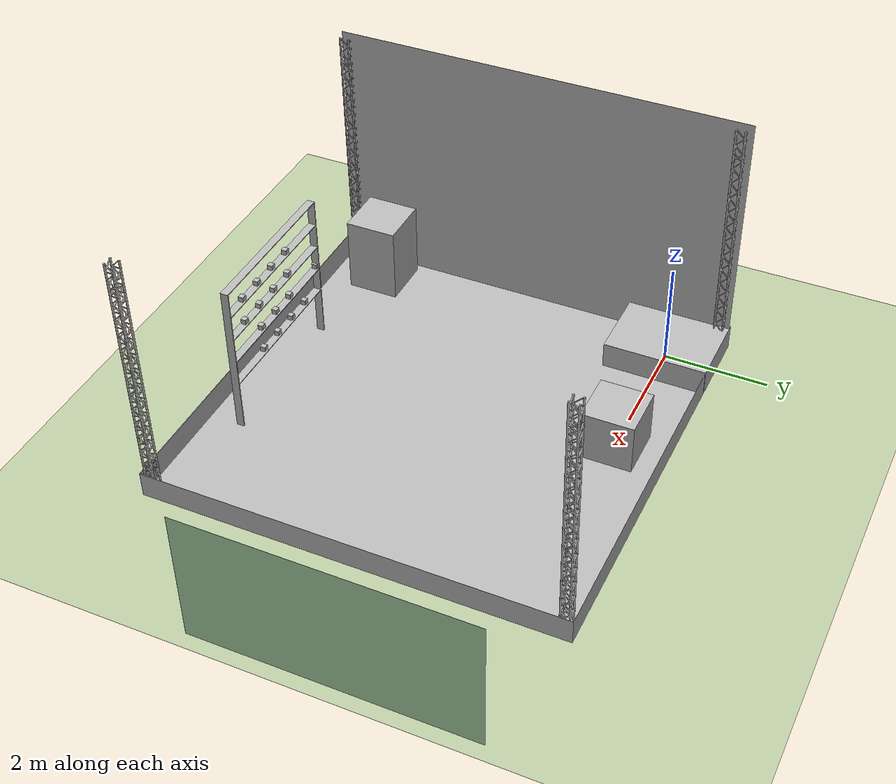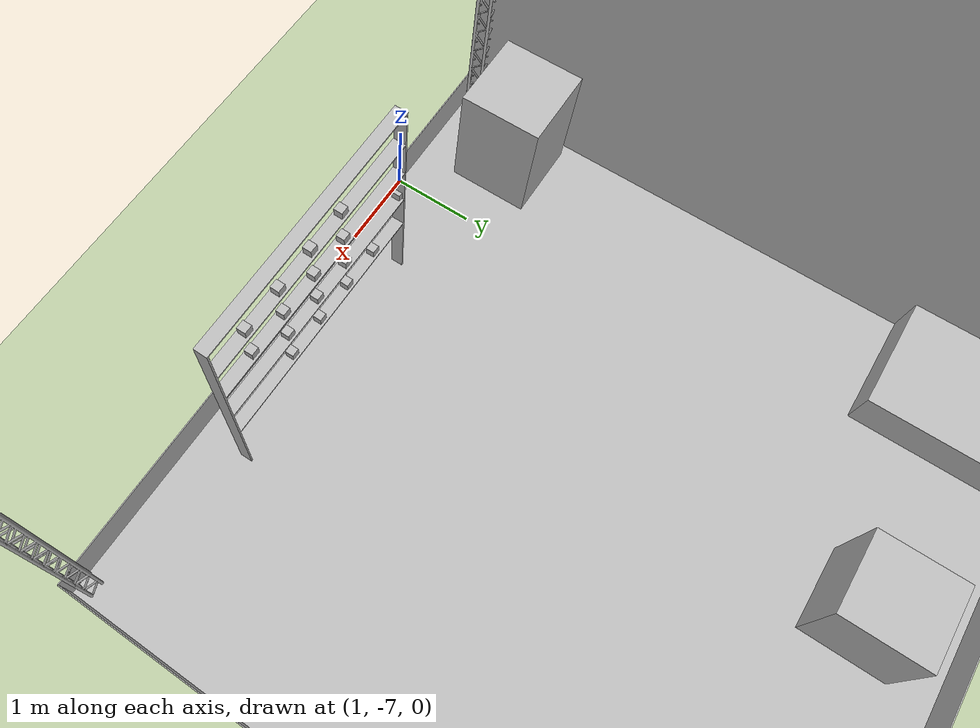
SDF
<?xml version="1.0" ?>
<?xml-model href="http://sdformat.org/schemas/root.xsd" schematypens="http://www.w3.org/2001/XMLSchema"?>
<sdf version="1.5">
  <world name="default">
    <plugin name="mrs_gazebo_static_transform_republisher_plugin" filename="libMrsGazeboCommonResources_StaticTransformRepublisher.so"/>

    <!-- coordinate system {-->
    <spherical_coordinates>
      <surface_model>EARTH_WGS84</surface_model>
      <latitude_deg>47.397743</latitude_deg>
      <longitude_deg>8.545594</longitude_deg>
      <elevation>0.0</elevation>
      <heading_deg>0</heading_deg>
    </spherical_coordinates>

    <!-- physics engine {-->
    <physics name="default_physics" default="0" type="ode">
      <gravity>0 0 -9.8066</gravity>
      <ode>
        <solver>
          <type>quick</type>
          <iters>50</iters>
          <sor>1.0</sor>
          <use_dynamic_moi_rescaling>0</use_dynamic_moi_rescaling>
        </solver>
        <constraints>
          <cfm>0</cfm>
          <erp>0.2</erp>
          <contact_max_correcting_vel>1000</contact_max_correcting_vel>
          <contact_surface_layer>0.001</contact_surface_layer>
        </constraints>
      </ode>
      <max_step_size>0.004</max_step_size>
      <real_time_factor>1</real_time_factor>
      <real_time_update_rate>250</real_time_update_rate>
      <magnetic_field>6.0e-06 2.3e-05 -4.2e-05</magnetic_field>
    </physics>

    <!-- setup shadows {-->
    <scene>
      <shadows>false</shadows>
    </scene>

    <!-- sun {-->
    <light type="directional" name="sun">
      <cast_shadows>true</cast_shadows>
      <pose>250 250 600 0 0 0</pose>
      <diffuse>0.8 0.8 0.8 1</diffuse>
      <specular>0.2 0.2 0.2 1</specular>
      <attenuation>
        <range>1000</range>
        <constant>0.9</constant>
        <linear>0.01</linear>
        <quadratic>0.001</quadratic>
      </attenuation>
      <direction>0 0 -1</direction>
    </light>

    <!-- ground plane {-->
    <model name="ground_plane">
      <static>true</static>
      <link name="link">
        <collision name="collision">
          <pose>0 0 0 0 0 0</pose>
          <geometry>
            <plane>
              <normal>0 0 1</normal>
              <size>250 250</size>
            </plane>
          </geometry>
          <surface>
            <friction>
              <ode>
                <mu>1</mu>
                <mu2>1</mu2>
              </ode>
            </friction>
          </surface>
        </collision>
        <visual name="grass">
          <pose>0 0 0 0 0 0</pose>
          <cast_shadows>false</cast_shadows>
          <geometry>
            <plane>
              <normal>0 0 1</normal>
              <size>150 250</size>
            </plane>
          </geometry>
          <material>
            <script>
              <uri>file://media/materials/scripts/Gazebo.material</uri>
              <name>Gazebo/Grass</name>
            </script>
          </material>
        </visual>
      </link>
    </model>

    <!-- GUI frame synchronization {-->
    <plugin name="mrs_gazebo_rviz_cam_synchronizer" filename="libMrsGazeboCommonResources_RvizCameraSynchronizer.so" >
      <target_frame_id>gazebo_user_camera</target_frame_id>
      <world_origin_frame_id>uav1/gps_origin</world_origin_frame_id>
      <frame_to_follow>uav1::base_link</frame_to_follow>
    </plugin>

    <!-- user camera {-->
    <gui>
      <camera name="camera">
        <pose>15 2 10 0 0.6 -2.64</pose>
      </camera>
    </gui>

    <!-- Models Worlds -->

    <!-- THE ARENA MODEL -->
    <model name="arena">
      <include>
        <uri>model://arena_spawn</uri>
        <!-- Pose ( x y z r p y ) -->
        <pose>-0.75 -7.0 0.001 0 -0 0</pose>
      </include>
    </model>

    <!-- THE TAKEOFF PLATFORM MODEL -->
    <model name="takeoff_platform">
      <include>
        <uri>model://takeoff_platform</uri>
        <pose>0.0 0.0 0.0 0.0 -0.0 0.0</pose>
      </include>
    </model>

    <!-- THE BANNER MODEL -->
    <model name="banner">
      <include>
        <uri>model://banner</uri>
        <pose>-0.75 -6.9 0.0 0.0 0.0 0.0</pose>
      </include>
    </model>

    <model name="banner_2">
      <include>
        <uri>model://banner_2</uri>
        <pose>-0.65 1.0 0.0 0.0 0.0 -1.57</pose>
      </include>
    </model>

    <!-- THE SUSPENDED LANDING PLATFORM MODEL -->
    <model name="landing_platform_A">
      <include>
        <uri>model://suspended_landing_platform</uri>
        <pose>2.75 0.0 1.0 0 -0 0</pose>
      </include>
    </model>

    <model name="landing_platform_E">
      <include>
        <uri>model://suspended_landing_platform</uri>
        <pose>0.0 -6.0 1.50 0 -0 0</pose>
      </include>
    </model>

    <!-- THE BARCODE SHELF -->
    <model name="barcodeshelf">
      <include>
        <uri>model://barcode_shelf</uri>
        <!-- Pose ( x y z r p y ) -->
        <pose frame=''>5.0 -6.45 0.0 0.0 -0.0 1.57</pose>
      </include>
    </model>

    <model name="box_A0">
      <include>
        <uri>model://box_A0</uri>
        <pose>4.0 -6.375 2.55 0 0 -0 </pose>
      </include>
    </model>

    <model name="box_A1">
      <include>
        <uri>model://box_A1</uri>
        <pose>4.5 -6.375 2.55 0 1.57 -0 </pose>
      </include>
    </model>

    <model name="box_A2">
      <include>
        <uri>model://box_A2</uri>
        <pose>3.0 -6.375 2.55 0 0 -0 </pose>
      </include>
    </model>

    <model name="box_A3">
      <include>
        <uri>model://box_A3</uri>
        <pose>3.5 -6.375 2.55 0 1.57 -0 </pose>
      </include>
    </model>

    <model name="box_B0">
      <include>
        <uri>model://box_B0</uri>
        <pose>3.5 -6.375 2.05 0 1.57 -0 </pose>
      </include>
    </model>

    <model name="box_B1">
      <include>
        <uri>model://box_B1</uri>
        <pose>4.0 -6.375 2.05 0 1.57 -0 </pose>
      </include>
    </model>

    <model name="box_B2">
      <include>
        <uri>model://box_B2</uri>
        <pose>3.0 -6.375 2.05 0 0 -0 </pose>
      </include>
    </model>

    <model name="box_B3">
      <include>
        <uri>model://box_B3</uri>
        <pose>4.5 -6.375 2.05 0 0 -0 </pose>
      </include>
    </model>

    <model name="box_C0">
      <include>
        <uri>model://box_C0</uri>
        <pose>3.5 -6.375 1.55 0 1.57 -0 </pose>
      </include>
    </model>

    <model name="box_C1">
      <include>
        <uri>model://box_C1</uri>
        <pose>2.0 -6.375 1.55 0 1.57 -0 </pose>
      </include>
    </model>

    <model name="box_C2">
      <include>
        <uri>model://box_C2</uri>
        <pose>3.0 -6.375 1.55 0 0 -0 </pose>
      </include>
    </model>

    <model name="box_C3">
      <include>
        <uri>model://box_C3</uri>
        <pose>4.0 -6.375 1.55 0 0 -0 </pose>
      </include>
    </model>

    <model name="box_D0">
      <include>
        <uri>model://box_D0</uri>
        <pose>3.0 -6.375 1.05 0 1.57 -0 </pose>
      </include>
    </model>

    <model name="box_D1">
      <include>
        <uri>model://box_D1</uri>
        <pose>4.0 -6.375 1.05 0 1.57 -0 </pose>
      </include>
    </model>

    <model name="box_D2">
      <include>
        <uri>model://box_D2</uri>
        <pose>2.5 -6.375 1.05 0 0 -0 </pose>
      </include>
    </model>

    <model name="box_D3">
      <include>
        <uri>model://box_D3</uri>
        <pose>3.5 -6.375 1.05 0 0 -0 </pose>
      </include>
    </model>

  </world>
</sdf>

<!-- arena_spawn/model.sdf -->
<sdf version='1.6'>
  <model name='arena_spawn'>
    <link name='link_arena'>
      <inertial>
        <mass>15</mass>
        <inertia>
          <ixx>1</ixx>
          <ixy>1</ixy>
          <ixz>1</ixz>
          <iyy>1</iyy>
          <iyz>1</iyz>
          <izz>1</izz>
        </inertia>
      </inertial>
      <self_collide>1</self_collide>
      <enable_wind>0</enable_wind>
      <kinematic>0</kinematic>
      <pose frame=''>0 0 0 0 -0 0</pose>
      <visual name='visual'>
        <pose frame=''>0 0 0 0 -0 0</pose>
        <geometry>
          <mesh>
            <uri>model://arena_spawn/meshes/Arena.obj</uri>
            <scale>1 1 1</scale>
          </mesh>
        </geometry>
        <transparency>0</transparency>
        <cast_shadows>1</cast_shadows>
      </visual>
      <collision name='collision'>
        <laser_retro>0</laser_retro>
        <max_contacts>10</max_contacts>
        <pose frame=''>0 0 0 0 -0 0</pose>
        <geometry>
          <mesh>
            <uri>model://arena_spawn/meshes/Arena.obj</uri>
            <scale>1 1 1</scale>
          </mesh>
        </geometry>
        <surface>
          <friction>
            <ode>
              <mu>1</mu>
              <mu2>1</mu2>
              <fdir1>0 0 0</fdir1>
              <slip1>0</slip1>
              <slip2>0</slip2>
            </ode>
            <torsional>
              <coefficient>1</coefficient>
              <patch_radius>100</patch_radius>
              <surface_radius>100</surface_radius>
              <use_patch_radius>1</use_patch_radius>
              <ode>
                <slip>0</slip>
              </ode>
            </torsional>
          </friction>
          <bounce>
            <restitution_coefficient>0</restitution_coefficient>
            <threshold>1e+06</threshold>
          </bounce>
          <contact>
            <collide_without_contact>0</collide_without_contact>
            <collide_without_contact_bitmask>1</collide_without_contact_bitmask>
            <collide_bitmask>1</collide_bitmask>
            <ode>
              <soft_cfm>0</soft_cfm>
              <soft_erp>0.2</soft_erp>
              <kp>1e+13</kp>
              <kd>1</kd>
              <max_vel>0.01</max_vel>
              <min_depth>0</min_depth>
            </ode>
            <bullet>
              <split_impulse>1</split_impulse>
              <split_impulse_penetration_threshold>-0.01</split_impulse_penetration_threshold>
              <soft_cfm>0</soft_cfm>
              <soft_erp>0.2</soft_erp>
              <kp>1e+13</kp>
              <kd>1</kd>
            </bullet>
          </contact>
        </surface>
      </collision>
    </link>
    <link name='pilar_1'>
      <inertial>
        <mass>1</mass>
        <inertia>
          <ixx>0.166667</ixx>
          <ixy>0</ixy>
          <ixz>0</ixz>
          <iyy>0.166667</iyy>
          <iyz>0</iyz>
          <izz>0.166667</izz>
        </inertia>
      </inertial>
      <self_collide>1</self_collide>
      <enable_wind>0</enable_wind>
      <kinematic>0</kinematic>
      <pose frame=''>0 0 0 0 -0 0</pose>
      <visual name='visual'>
        <pose frame=''>0 0 0 0 -0 0</pose>
        <geometry>
          <mesh>
            <uri>model://arena_spawn/meshes/pilar.obj</uri>
            <scale>1 1 1</scale>
          </mesh>
        </geometry>
        <transparency>0</transparency>
        <cast_shadows>1</cast_shadows>
      </visual>
      <collision name='collision'>
        <laser_retro>0</laser_retro>
        <max_contacts>10</max_contacts>
        <pose frame=''>0 0 0 0 -0 0</pose>
        <geometry>
          <mesh>
            <uri>model://arena_spawn/meshes/pilar.obj</uri>
            <scale>1 1 1</scale>
          </mesh>
        </geometry>
        <surface>
          <friction>
            <ode>
              <mu>1</mu>
              <mu2>1</mu2>
              <fdir1>0 0 0</fdir1>
              <slip1>0</slip1>
              <slip2>0</slip2>
            </ode>
            <torsional>
              <coefficient>1</coefficient>
              <patch_radius>100</patch_radius>
              <surface_radius>100</surface_radius>
              <use_patch_radius>1</use_patch_radius>
              <ode>
                <slip>0</slip>
              </ode>
            </torsional>
          </friction>
          <bounce>
            <restitution_coefficient>0</restitution_coefficient>
            <threshold>1e+06</threshold>
          </bounce>
          <contact>
            <collide_without_contact>0</collide_without_contact>
            <collide_without_contact_bitmask>1</collide_without_contact_bitmask>
            <collide_bitmask>1</collide_bitmask>
            <ode>
              <soft_cfm>0</soft_cfm>
              <soft_erp>0.2</soft_erp>
              <kp>1e+13</kp>
              <kd>1</kd>
              <max_vel>0.01</max_vel>
              <min_depth>0</min_depth>
            </ode>
            <bullet>
              <split_impulse>1</split_impulse>
              <split_impulse_penetration_threshold>-0.01</split_impulse_penetration_threshold>
              <soft_cfm>0</soft_cfm>
              <soft_erp>0.2</soft_erp>
              <kp>1e+13</kp>
              <kd>1</kd>
            </bullet>
          </contact>
        </surface>
      </collision>
    </link>
    <link name='pilar_2'>
      <inertial>
        <mass>1</mass>
        <inertia>
          <ixx>0.166667</ixx>
          <ixy>0</ixy>
          <ixz>0</ixz>
          <iyy>0.166667</iyy>
          <iyz>0</iyz>
          <izz>0.166667</izz>
        </inertia>
      </inertial>
      <self_collide>1</self_collide>
      <enable_wind>0</enable_wind>
      <kinematic>0</kinematic>
      <pose frame=''>7.7 0 0 0 -0 0</pose>
      <visual name='visual'>
        <pose frame=''>0 0 0 0 -0 0</pose>
        <geometry>
          <mesh>
            <uri>model://arena_spawn/meshes/pilar.obj</uri>
            <scale>1 1 1</scale>
          </mesh>
        </geometry>
        <transparency>0</transparency>
        <cast_shadows>1</cast_shadows>
      </visual>
      <collision name='collision'>
        <laser_retro>0</laser_retro>
        <max_contacts>10</max_contacts>
        <pose frame=''>0 0 0 0 -0 0</pose>
        <geometry>
          <mesh>
            <uri>model://arena_spawn/meshes/pilar.obj</uri>
            <scale>1 1 1</scale>
          </mesh>
        </geometry>
        <surface>
          <friction>
            <ode>
              <mu>1</mu>
              <mu2>1</mu2>
              <fdir1>0 0 0</fdir1>
              <slip1>0</slip1>
              <slip2>0</slip2>
            </ode>
            <torsional>
              <coefficient>1</coefficient>
              <patch_radius>100</patch_radius>
              <surface_radius>100</surface_radius>
              <use_patch_radius>1</use_patch_radius>
              <ode>
                <slip>0</slip>
              </ode>
            </torsional>
          </friction>
          <bounce>
            <restitution_coefficient>0</restitution_coefficient>
            <threshold>1e+06</threshold>
          </bounce>
          <contact>
            <collide_without_contact>0</collide_without_contact>
            <collide_without_contact_bitmask>1</collide_without_contact_bitmask>
            <collide_bitmask>1</collide_bitmask>
            <ode>
              <soft_cfm>0</soft_cfm>
              <soft_erp>0.2</soft_erp>
              <kp>1e+13</kp>
              <kd>1</kd>
              <max_vel>0.01</max_vel>
              <min_depth>0</min_depth>
            </ode>
            <bullet>
              <split_impulse>1</split_impulse>
              <split_impulse_penetration_threshold>-0.01</split_impulse_penetration_threshold>
              <soft_cfm>0</soft_cfm>
              <soft_erp>0.2</soft_erp>
              <kp>1e+13</kp>
              <kd>1</kd>
            </bullet>
          </contact>
        </surface>
      </collision>
    </link>
    <link name='pilar_3'>
      <inertial>
        <mass>1</mass>
        <inertia>
          <ixx>0.166667</ixx>
          <ixy>0</ixy>
          <ixz>0</ixz>
          <iyy>0.166667</iyy>
          <iyz>0</iyz>
          <izz>0.166667</izz>
        </inertia>
      </inertial>
      <self_collide>1</self_collide>
      <enable_wind>0</enable_wind>
      <kinematic>0</kinematic>
      <pose frame=''>0 7.7 0 0 -0 0</pose>
      <visual name='visual'>
        <pose frame=''>0 0 0 0 -0 0</pose>
        <geometry>
          <mesh>
            <uri>model://arena_spawn/meshes/pilar.obj</uri>
            <scale>1 1 1</scale>
          </mesh>
        </geometry>
        <transparency>0</transparency>
        <cast_shadows>1</cast_shadows>
      </visual>
      <collision name='collision'>
        <laser_retro>0</laser_retro>
        <max_contacts>10</max_contacts>
        <pose frame=''>0 0 0 0 -0 0</pose>
        <geometry>
          <mesh>
            <uri>model://arena_spawn/meshes/pilar.obj</uri>
            <scale>1 1 1</scale>
          </mesh>
        </geometry>
        <surface>
          <friction>
            <ode>
              <mu>1</mu>
              <mu2>1</mu2>
              <fdir1>0 0 0</fdir1>
              <slip1>0</slip1>
              <slip2>0</slip2>
            </ode>
            <torsional>
              <coefficient>1</coefficient>
              <patch_radius>100</patch_radius>
              <surface_radius>100</surface_radius>
              <use_patch_radius>1</use_patch_radius>
              <ode>
                <slip>0</slip>
              </ode>
            </torsional>
          </friction>
          <bounce>
            <restitution_coefficient>0</restitution_coefficient>
            <threshold>1e+06</threshold>
          </bounce>
          <contact>
            <collide_without_contact>0</collide_without_contact>
            <collide_without_contact_bitmask>1</collide_without_contact_bitmask>
            <collide_bitmask>1</collide_bitmask>
            <ode>
              <soft_cfm>0</soft_cfm>
              <soft_erp>0.2</soft_erp>
              <kp>1e+13</kp>
              <kd>1</kd>
              <max_vel>0.01</max_vel>
              <min_depth>0</min_depth>
            </ode>
            <bullet>
              <split_impulse>1</split_impulse>
              <split_impulse_penetration_threshold>-0.01</split_impulse_penetration_threshold>
              <soft_cfm>0</soft_cfm>
              <soft_erp>0.2</soft_erp>
              <kp>1e+13</kp>
              <kd>1</kd>
            </bullet>
          </contact>
        </surface>
      </collision>
    </link>
    <link name='pilar_4'>
      <inertial>
        <mass>1</mass>
        <inertia>
          <ixx>0.166667</ixx>
          <ixy>0</ixy>
          <ixz>0</ixz>
          <iyy>0.166667</iyy>
          <iyz>0</iyz>
          <izz>0.166667</izz>
        </inertia>
      </inertial>
      <self_collide>1</self_collide>
      <enable_wind>0</enable_wind>
      <kinematic>0</kinematic>
      <pose frame=''>7.7 7.7 0 0 -0 0</pose>
      <visual name='visual'>
        <pose frame=''>0 0 0 0 -0 0</pose>
        <geometry>
          <mesh>
            <uri>model://arena_spawn/meshes/pilar.obj</uri>
            <scale>1 1 1</scale>
          </mesh>
        </geometry>
        <transparency>0</transparency>
        <cast_shadows>1</cast_shadows>
      </visual>
      <collision name='collision'>
        <laser_retro>0</laser_retro>
        <max_contacts>10</max_contacts>
        <pose frame=''>0 0 0 0 -0 0</pose>
        <geometry>
          <mesh>
            <uri>model://arena_spawn/meshes/pilar.obj</uri>
            <scale>1 1 1</scale>
          </mesh>
        </geometry>
        <surface>
          <friction>
            <ode>
              <mu>1</mu>
              <mu2>1</mu2>
              <fdir1>0 0 0</fdir1>
              <slip1>0</slip1>
              <slip2>0</slip2>
            </ode>
            <torsional>
              <coefficient>1</coefficient>
              <patch_radius>100</patch_radius>
              <surface_radius>100</surface_radius>
              <use_patch_radius>1</use_patch_radius>
              <ode>
                <slip>0</slip>
              </ode>
            </torsional>
          </friction>
          <bounce>
            <restitution_coefficient>0</restitution_coefficient>
            <threshold>1e+06</threshold>
          </bounce>
          <contact>
            <collide_without_contact>0</collide_without_contact>
            <collide_without_contact_bitmask>1</collide_without_contact_bitmask>
            <collide_bitmask>1</collide_bitmask>
            <ode>
              <soft_cfm>0</soft_cfm>
              <soft_erp>0.2</soft_erp>
              <kp>1e+13</kp>
              <kd>1</kd>
              <max_vel>0.01</max_vel>
              <min_depth>0</min_depth>
            </ode>
            <bullet>
              <split_impulse>1</split_impulse>
              <split_impulse_penetration_threshold>-0.01</split_impulse_penetration_threshold>
              <soft_cfm>0</soft_cfm>
              <soft_erp>0.2</soft_erp>
              <kp>1e+13</kp>
              <kd>1</kd>
            </bullet>
          </contact>
        </surface>
      </collision>
    </link>
    <static>1</static>
    <pose frame=''>0 0 0.0005 0 -0 0</pose>
  </model>
</sdf>

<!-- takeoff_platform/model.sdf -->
<sdf version='1.6'>
  <model name='takeoff_platform'>
    <link name='link_takeoff_platform'>
      <inertial>
        <mass>15</mass>
        <inertia>
          <ixx>1</ixx>
          <ixy>0</ixy>
          <ixz>0</ixz>
          <iyy>1</iyy>
          <iyz>0</iyz>
          <izz>1</izz>
        </inertia>
      </inertial>
      <self_collide>1</self_collide>
      <enable_wind>0</enable_wind>
      <kinematic>0</kinematic>
      <pose frame=''>0 0 0 0 -0 0</pose>
      <visual name='visual'>
        <pose frame=''>0 0 0 0 -0 0</pose>
        <geometry>
          <mesh>
            <uri>model://takeoff_platform/meshes/takeoff_platform.obj</uri>
            <scale>1 1 1</scale>
          </mesh>
        </geometry>
        <transparency>0</transparency>
        <cast_shadows>1</cast_shadows>
      </visual>
      <collision name='collision'>
        <laser_retro>0</laser_retro>
        <max_contacts>10</max_contacts>
        <pose frame=''>0 0 0 0 -0 0</pose>
        <geometry>
          <mesh>
            <uri>model://takeoff_platform/meshes/takeoff_platform.obj</uri>
            <scale>1 1 1</scale>
          </mesh>
        </geometry>
        <surface>
          <friction>
            <ode>
              <mu>1</mu>
              <mu2>1</mu2>
              <fdir1>0 0 0</fdir1>
              <slip1>0</slip1>
              <slip2>0</slip2>
            </ode>
            <torsional>
              <coefficient>1</coefficient>
              <patch_radius>100</patch_radius>
              <surface_radius>100</surface_radius>
              <use_patch_radius>1</use_patch_radius>
              <ode>
                <slip>0</slip>
              </ode>
            </torsional>
          </friction>
          <bounce>
            <restitution_coefficient>0</restitution_coefficient>
            <threshold>1e+06</threshold>
          </bounce>
          <contact>
            <collide_without_contact>0</collide_without_contact>
            <collide_without_contact_bitmask>1</collide_without_contact_bitmask>
            <collide_bitmask>1</collide_bitmask>
            <ode>
              <soft_cfm>0</soft_cfm>
              <soft_erp>0.2</soft_erp>
              <kp>1e+13</kp>
              <kd>1</kd>
              <max_vel>0.01</max_vel>
              <min_depth>0</min_depth>
            </ode>
            <bullet>
              <split_impulse>1</split_impulse>
              <split_impulse_penetration_threshold>-0.01</split_impulse_penetration_threshold>
              <soft_cfm>0</soft_cfm>
              <soft_erp>0.2</soft_erp>
              <kp>1e+13</kp>
              <kd>1</kd>
            </bullet>
          </contact>
        </surface>
      </collision>
    </link>
    <static>1</static>
    <pose frame=''>0 0 0.0005 0 -0 0</pose>
  </model>
</sdf>

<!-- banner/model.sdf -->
<sdf version='1.6'>
  <model name='banner'>
    <link name='link_0'>
      <inertial>
        <mass>1</mass>
        <inertia>
          <ixx>0.166667</ixx>
          <ixy>0</ixy>
          <ixz>0</ixz>
          <iyy>0.166667</iyy>
          <iyz>0</iyz>
          <izz>0.166667</izz>
        </inertia>
      </inertial>
      <pose>0 0 0 0 -0 0</pose>
      <visual name='visual'>
        <pose>0 0 0 0 -0 0</pose>
        <geometry>
          <mesh>
            <uri>model://banner/meshes/banner.obj</uri>
            <scale>1.0 1.0 1.0</scale>
          </mesh>
        </geometry>
        <transparency>0</transparency>
        <cast_shadows>1</cast_shadows>
      </visual>
      <collision name='collision'>
        <laser_retro>0</laser_retro>
        <max_contacts>10</max_contacts>
        <pose>0 0 0 0 -0 0</pose>
        <geometry>
          <mesh>
            <uri>model://banner/meshes/banner.obj</uri>
            <scale>1.0 1.0 1.0</scale>
          </mesh>
        </geometry>
      </collision>
    </link>
    <static>1</static>
    <allow_auto_disable>1</allow_auto_disable>
  </model>
</sdf>

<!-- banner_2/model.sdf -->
<sdf version='1.6'>
  <model name='banner_2'>
    <link name='link_0'>
      <inertial>
        <mass>1</mass>
        <inertia>
          <ixx>0.166667</ixx>
          <ixy>0</ixy>
          <ixz>0</ixz>
          <iyy>0.166667</iyy>
          <iyz>0</iyz>
          <izz>0.166667</izz>
        </inertia>
      </inertial>
      <pose>0 0 0 0 -0 0</pose>
      <visual name='visual'>
        <pose>0 0 0 0 -0 0</pose>
        <geometry>
          <mesh>
            <uri>model://banner_2/meshes/banner.obj</uri>
            <scale>1.0 1.0 1.0</scale>
          </mesh>
        </geometry>
        <transparency>0</transparency>
        <cast_shadows>1</cast_shadows>
      </visual>
      <collision name='collision'>
        <laser_retro>0</laser_retro>
        <max_contacts>10</max_contacts>
        <pose>0 0 0 0 -0 0</pose>
        <geometry>
          <mesh>
            <uri>model://banner_2/meshes/banner.obj</uri>
            <scale>1.0 1.0 1.0</scale>
          </mesh>
        </geometry>
      </collision>
    </link>
    <static>1</static>
    <allow_auto_disable>1</allow_auto_disable>
  </model>
</sdf>

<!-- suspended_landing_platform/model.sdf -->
<sdf version='1.6'>
  <model name='suspended_landing_platform'>
    <link name='link_suspended_landing_platform'>
      <inertial>
        <mass>1</mass>
        <inertia>
          <ixx>0.166667</ixx>
          <ixy>0</ixy>
          <ixz>0</ixz>
          <iyy>0.166667</iyy>
          <iyz>0</iyz>
          <izz>0.166667</izz>
        </inertia>
        <pose>0 0 0 0 -0 0</pose>
      </inertial>
      <self_collide>0</self_collide>
      <enable_wind>0</enable_wind>
      <kinematic>0</kinematic>
      <pose>0 0 0 0 -0 0</pose>
      <gravity>1</gravity>
      <visual name='visual'>
        <pose frame=''>0 0 0 0 -0 0</pose>
        <geometry>
          <mesh>
            <uri>model://suspended_landing_platform/meshes/suspended_landing_platform.obj</uri>
            <scale>1 1 1</scale>
          </mesh>
        </geometry>
        <transparency>0</transparency>
        <cast_shadows>1</cast_shadows>
      </visual>
      <collision name='collision'>
        <laser_retro>0</laser_retro>
        <max_contacts>10</max_contacts>
        <pose>0 0 -0.75 0 -0 0</pose>
        <geometry>
          <box>
            <size>1 1 1.5</size>
          </box>
        </geometry>
        <surface>
          <friction>
            <ode>
              <mu>100</mu>
              <mu2>100</mu2>
              <fdir1>0 0 0</fdir1>
              <slip1>0</slip1>
              <slip2>0</slip2>
            </ode>
            <torsional>
              <coefficient>1</coefficient>
              <patch_radius>1</patch_radius>
              <surface_radius>1</surface_radius>
              <use_patch_radius>1</use_patch_radius>
              <ode>
                <slip>0</slip>
              </ode>
            </torsional>
          </friction>
          <bounce>
            <restitution_coefficient>1</restitution_coefficient>
            <threshold>1e+06</threshold>
          </bounce>
          <contact>
            <collide_without_contact>0</collide_without_contact>
            <collide_without_contact_bitmask>1</collide_without_contact_bitmask>
            <collide_bitmask>1</collide_bitmask>
            <ode>
              <soft_cfm>0</soft_cfm>
              <soft_erp>0.2</soft_erp>
              <kp>1e+13</kp>
              <kd>1</kd>
              <max_vel>0.01</max_vel>
              <min_depth>0</min_depth>
            </ode>
            <bullet>
              <split_impulse>1</split_impulse>
              <split_impulse_penetration_threshold>-0.01</split_impulse_penetration_threshold>
              <soft_cfm>0</soft_cfm>
              <soft_erp>0.2</soft_erp>
              <kp>1e+13</kp>
              <kd>1</kd>
            </bullet>
          </contact>
        </surface>
      </collision>
    </link>
    <static>1</static>
    <allow_auto_disable>1</allow_auto_disable>
  </model>
</sdf>

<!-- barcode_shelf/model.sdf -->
<sdf version='1.7'>
  <model name='barcode_shelf'>
    <link name='link_barcode_shelf'>
      <inertial>
        <mass>1</mass>
        <inertia>
          <ixx>0.166667</ixx>
          <ixy>0</ixy>
          <ixz>0</ixz>
          <iyy>0.166667</iyy>
          <iyz>0</iyz>
          <izz>0.166667</izz>
        </inertia>
      </inertial>
      <pose>0 0 0 1.5708 -0 0</pose>
      <visual name='visual'>
        <pose>0 0 0 0 -0 0</pose>
        <geometry>
          <mesh>
            <uri>model://barcode_shelf/meshes/shelf.obj</uri>
            <scale>1 1 1</scale>
          </mesh>
        </geometry>
        <transparency>0</transparency>
        <cast_shadows>1</cast_shadows>
      </visual>
      <collision name='collision'>
        <laser_retro>0</laser_retro>
        <max_contacts>10</max_contacts>
        <pose>0 0 0 0 -0 0</pose>
        <geometry>
          <mesh>
            <uri>model://barcode_shelf/meshes/shelf.obj</uri>
            <scale>1 1 1</scale>
          </mesh>
        </geometry>
        <surface>
          <friction>
            <ode>
              <mu>1</mu>
              <mu2>1</mu2>
              <fdir1>0 0 0</fdir1>
              <slip1>0</slip1>
              <slip2>0</slip2>
            </ode>
            <torsional>
              <coefficient>1</coefficient>
              <patch_radius>0</patch_radius>
              <surface_radius>0</surface_radius>
              <use_patch_radius>1</use_patch_radius>
              <ode>
                <slip>0</slip>
              </ode>
            </torsional>
          </friction>
          <bounce>
            <restitution_coefficient>0</restitution_coefficient>
            <threshold>1e+06</threshold>
          </bounce>
          <contact>
            <collide_without_contact>0</collide_without_contact>
            <collide_without_contact_bitmask>1</collide_without_contact_bitmask>
            <collide_bitmask>1</collide_bitmask>
            <ode>
              <soft_cfm>0</soft_cfm>
              <soft_erp>0.2</soft_erp>
              <kp>1e+13</kp>
              <kd>1</kd>
              <max_vel>0.01</max_vel>
              <min_depth>0</min_depth>
            </ode>
            <bullet>
              <split_impulse>1</split_impulse>
              <split_impulse_penetration_threshold>-0.01</split_impulse_penetration_threshold>
              <soft_cfm>0</soft_cfm>
              <soft_erp>0.2</soft_erp>
              <kp>1e+13</kp>
              <kd>1</kd>
            </bullet>
          </contact>
        </surface>
      </collision>
    </link>
    <static>1</static>
    <allow_auto_disable>1</allow_auto_disable>
  </model>
</sdf>

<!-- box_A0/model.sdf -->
<sdf version='1.6'>
  <model name='box_A0'>
    <link name='link_box_A0'>
      <inertial>
        <mass>0.160</mass>
        <inertia>
          <ixx>0.000272</ixx>
          <ixy>0</ixy>
          <ixz>0</ixz>
          <iyy>0.000272</iyy>
          <iyz>0</iyz>
          <izz>0.000272</izz>
        </inertia>
        <pose>0 0 0 0 -0 0</pose>
      </inertial>
      <self_collide>0</self_collide>
      <enable_wind>0</enable_wind>
      <kinematic>0</kinematic>
      <pose>0 0 0 0 -0 0</pose>
      <gravity>1</gravity>
      <visual name='visual'>
        <pose frame=''>0 0 0 0 -0 0</pose>
        <geometry>
          <mesh>
            <uri>model://box_A0/meshes/codebar_box.obj</uri>
            <scale>1 1 1</scale>
          </mesh>
        </geometry>
        <transparency>0</transparency>
        <cast_shadows>1</cast_shadows>
      </visual>
      <collision name='collision'>
        <laser_retro>1</laser_retro>
        <max_contacts>100000</max_contacts>
        <pose>0 0 0 0 -0 0</pose>
        <geometry>
          <box>
            <size>0.1 0.1 0.1</size>
          </box>
        </geometry>
        <surface>
          <friction>
            <ode>
              <mu>1</mu>
              <mu2>1</mu2>
              <fdir1>0 0 0</fdir1>
              <slip1>0</slip1>
              <slip2>0</slip2>
            </ode>
            <torsional>
              <coefficient>1</coefficient>
              <patch_radius>1</patch_radius>
              <surface_radius>1</surface_radius>
              <use_patch_radius>1</use_patch_radius>
              <ode>
                <slip>0</slip>
              </ode>
            </torsional>
          </friction>
          <bounce>
            <restitution_coefficient>0</restitution_coefficient>
            <threshold>1e+06</threshold>
          </bounce>
          <contact>
            <collide_without_contact>0</collide_without_contact>
            <collide_without_contact_bitmask>1</collide_without_contact_bitmask>
            <collide_bitmask>1</collide_bitmask>
            <ode>
              <soft_cfm>0</soft_cfm>
              <soft_erp>0.2</soft_erp>
              <kp>1e+13</kp>
              <kd>1</kd>
              <max_vel>0.01</max_vel>
              <min_depth>0</min_depth>
            </ode>
            <bullet>
              <split_impulse>1</split_impulse>
              <split_impulse_penetration_threshold>-0.01</split_impulse_penetration_threshold>
              <soft_cfm>0</soft_cfm>
              <soft_erp>0.2</soft_erp>
              <kp>1e+13</kp>
              <kd>1</kd>
            </bullet>
          </contact>
        </surface>
      </collision>
    </link>
    <static>1</static>
    <allow_Auto_disable>1</allow_Auto_disable>
  </model>
</sdf>

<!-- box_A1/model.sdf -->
<sdf version='1.6'>
  <model name='box_A1'>
    <link name='link_box_A1'>
      <inertial>
        <mass>0.160</mass>
        <inertia>
          <ixx>0.000272</ixx>
          <ixy>0</ixy>
          <ixz>0</ixz>
          <iyy>0.000272</iyy>
          <iyz>0</iyz>
          <izz>0.000272</izz>
        </inertia>
        <pose>0 0 0 0 -0 0</pose>
      </inertial>
      <self_collide>0</self_collide>
      <enable_wind>0</enable_wind>
      <kinematic>0</kinematic>
      <pose>0 0 0 0 -0 0</pose>
      <gravity>1</gravity>
      <visual name='visual'>
        <pose frame=''>0 0 0 0 -0 0</pose>
        <geometry>
          <mesh>
            <uri>model://box_A1/meshes/codebar_box.obj</uri>
            <scale>1 1 1</scale>
          </mesh>
        </geometry>
        <transparency>0</transparency>
        <cast_shadows>1</cast_shadows>
      </visual>
      <collision name='collision'>
        <laser_retro>1</laser_retro>
        <max_contacts>100000</max_contacts>
        <pose>0 0 0 0 -0 0</pose>
        <geometry>
          <box>
            <size>0.1 0.1 0.1</size>
          </box>
        </geometry>
        <surface>
          <friction>
            <ode>
              <mu>1</mu>
              <mu2>1</mu2>
              <fdir1>0 0 0</fdir1>
              <slip1>0</slip1>
              <slip2>0</slip2>
            </ode>
            <torsional>
              <coefficient>1</coefficient>
              <patch_radius>1</patch_radius>
              <surface_radius>1</surface_radius>
              <use_patch_radius>1</use_patch_radius>
              <ode>
                <slip>0</slip>
              </ode>
            </torsional>
          </friction>
          <bounce>
            <restitution_coefficient>0</restitution_coefficient>
            <threshold>1e+06</threshold>
          </bounce>
          <contact>
            <collide_without_contact>0</collide_without_contact>
            <collide_without_contact_bitmask>1</collide_without_contact_bitmask>
            <collide_bitmask>1</collide_bitmask>
            <ode>
              <soft_cfm>0</soft_cfm>
              <soft_erp>0.2</soft_erp>
              <kp>1e+13</kp>
              <kd>1</kd>
              <max_vel>0.01</max_vel>
              <min_depth>0</min_depth>
            </ode>
            <bullet>
              <split_impulse>1</split_impulse>
              <split_impulse_penetration_threshold>-0.01</split_impulse_penetration_threshold>
              <soft_cfm>0</soft_cfm>
              <soft_erp>0.2</soft_erp>
              <kp>1e+13</kp>
              <kd>1</kd>
            </bullet>
          </contact>
        </surface>
      </collision>
    </link>
    <static>1</static>
    <allow_Auto_disable>1</allow_Auto_disable>
  </model>
</sdf>

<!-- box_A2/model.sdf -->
<sdf version='1.6'>
  <model name='box_A2'>
    <link name='link_box_A2'>
      <inertial>
        <mass>0.160</mass>
        <inertia>
          <ixx>0.000272</ixx>
          <ixy>0</ixy>
          <ixz>0</ixz>
          <iyy>0.000272</iyy>
          <iyz>0</iyz>
          <izz>0.000272</izz>
        </inertia>
        <pose>0 0 0 0 -0 0</pose>
      </inertial>
      <self_collide>0</self_collide>
      <enable_wind>0</enable_wind>
      <kinematic>0</kinematic>
      <pose>0 0 0 0 -0 0</pose>
      <gravity>1</gravity>
      <visual name='visual'>
        <pose frame=''>0 0 0 0 -0 0</pose>
        <geometry>
          <mesh>
            <uri>model://box_A2/meshes/codebar_box.obj</uri>
            <scale>1 1 1</scale>
          </mesh>
        </geometry>
        <transparency>0</transparency>
        <cast_shadows>1</cast_shadows>
      </visual>
      <collision name='collision'>
        <laser_retro>1</laser_retro>
        <max_contacts>100000</max_contacts>
        <pose>0 0 0 0 -0 0</pose>
        <geometry>
          <box>
            <size>0.1 0.1 0.1</size>
          </box>
        </geometry>
        <surface>
          <friction>
            <ode>
              <mu>1</mu>
              <mu2>1</mu2>
              <fdir1>0 0 0</fdir1>
              <slip1>0</slip1>
              <slip2>0</slip2>
            </ode>
            <torsional>
              <coefficient>1</coefficient>
              <patch_radius>1</patch_radius>
              <surface_radius>1</surface_radius>
              <use_patch_radius>1</use_patch_radius>
              <ode>
                <slip>0</slip>
              </ode>
            </torsional>
          </friction>
          <bounce>
            <restitution_coefficient>0</restitution_coefficient>
            <threshold>1e+06</threshold>
          </bounce>
          <contact>
            <collide_without_contact>0</collide_without_contact>
            <collide_without_contact_bitmask>1</collide_without_contact_bitmask>
            <collide_bitmask>1</collide_bitmask>
            <ode>
              <soft_cfm>0</soft_cfm>
              <soft_erp>0.2</soft_erp>
              <kp>1e+13</kp>
              <kd>1</kd>
              <max_vel>0.01</max_vel>
              <min_depth>0</min_depth>
            </ode>
            <bullet>
              <split_impulse>1</split_impulse>
              <split_impulse_penetration_threshold>-0.01</split_impulse_penetration_threshold>
              <soft_cfm>0</soft_cfm>
              <soft_erp>0.2</soft_erp>
              <kp>1e+13</kp>
              <kd>1</kd>
            </bullet>
          </contact>
        </surface>
      </collision>
    </link>
    <static>1</static>
    <allow_Auto_disable>1</allow_Auto_disable>
  </model>
</sdf>

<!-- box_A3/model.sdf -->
<sdf version='1.6'>
  <model name='box_A3'>
    <link name='link_box_A3'>
      <inertial>
        <mass>0.160</mass>
        <inertia>
          <ixx>0.000272</ixx>
          <ixy>0</ixy>
          <ixz>0</ixz>
          <iyy>0.000272</iyy>
          <iyz>0</iyz>
          <izz>0.000272</izz>
        </inertia>
        <pose>0 0 0 0 -0 0</pose>
      </inertial>
      <self_collide>0</self_collide>
      <enable_wind>0</enable_wind>
      <kinematic>0</kinematic>
      <pose>0 0 0 0 -0 0</pose>
      <gravity>1</gravity>
      <visual name='visual'>
        <pose frame=''>0 0 0 0 -0 0</pose>
        <geometry>
          <mesh>
            <uri>model://box_A3/meshes/codebar_box.obj</uri>
            <scale>1 1 1</scale>
          </mesh>
        </geometry>
        <transparency>0</transparency>
        <cast_shadows>1</cast_shadows>
      </visual>
      <collision name='collision'>
        <laser_retro>1</laser_retro>
        <max_contacts>100000</max_contacts>
        <pose>0 0 0 0 -0 0</pose>
        <geometry>
          <box>
            <size>0.1 0.1 0.1</size>
          </box>
        </geometry>
        <surface>
          <friction>
            <ode>
              <mu>1</mu>
              <mu2>1</mu2>
              <fdir1>0 0 0</fdir1>
              <slip1>0</slip1>
              <slip2>0</slip2>
            </ode>
            <torsional>
              <coefficient>1</coefficient>
              <patch_radius>1</patch_radius>
              <surface_radius>1</surface_radius>
              <use_patch_radius>1</use_patch_radius>
              <ode>
                <slip>0</slip>
              </ode>
            </torsional>
          </friction>
          <bounce>
            <restitution_coefficient>0</restitution_coefficient>
            <threshold>1e+06</threshold>
          </bounce>
          <contact>
            <collide_without_contact>0</collide_without_contact>
            <collide_without_contact_bitmask>1</collide_without_contact_bitmask>
            <collide_bitmask>1</collide_bitmask>
            <ode>
              <soft_cfm>0</soft_cfm>
              <soft_erp>0.2</soft_erp>
              <kp>1e+13</kp>
              <kd>1</kd>
              <max_vel>0.01</max_vel>
              <min_depth>0</min_depth>
            </ode>
            <bullet>
              <split_impulse>1</split_impulse>
              <split_impulse_penetration_threshold>-0.01</split_impulse_penetration_threshold>
              <soft_cfm>0</soft_cfm>
              <soft_erp>0.2</soft_erp>
              <kp>1e+13</kp>
              <kd>1</kd>
            </bullet>
          </contact>
        </surface>
      </collision>
    </link>
    <static>1</static>
    <allow_Auto_disable>1</allow_Auto_disable>
  </model>
</sdf>

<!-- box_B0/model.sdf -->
<sdf version='1.6'>
  <model name='box_B0'>
    <link name='link_box_B0'>
      <inertial>
        <mass>0.160</mass>
        <inertia>
          <ixx>0.000272</ixx>
          <ixy>0</ixy>
          <ixz>0</ixz>
          <iyy>0.000272</iyy>
          <iyz>0</iyz>
          <izz>0.000272</izz>
        </inertia>
        <pose>0 0 0 0 -0 0</pose>
      </inertial>
      <self_collide>0</self_collide>
      <enable_wind>0</enable_wind>
      <kinematic>0</kinematic>
      <pose>0 0 0 0 -0 0</pose>
      <gravity>1</gravity>
      <visual name='visual'>
        <pose frame=''>0 0 0 0 -0 0</pose>
        <geometry>
          <mesh>
            <uri>model://box_B0/meshes/codebar_box.obj</uri>
            <scale>1 1 1</scale>
          </mesh>
        </geometry>
        <transparency>0</transparency>
        <cast_shadows>1</cast_shadows>
      </visual>
      <collision name='collision'>
        <laser_retro>1</laser_retro>
        <max_contacts>100000</max_contacts>
        <pose>0 0 0 0 -0 0</pose>
        <geometry>
          <box>
            <size>0.1 0.1 0.1</size>
          </box>
        </geometry>
        <surface>
          <friction>
            <ode>
              <mu>1</mu>
              <mu2>1</mu2>
              <fdir1>0 0 0</fdir1>
              <slip1>0</slip1>
              <slip2>0</slip2>
            </ode>
            <torsional>
              <coefficient>1</coefficient>
              <patch_radius>1</patch_radius>
              <surface_radius>1</surface_radius>
              <use_patch_radius>1</use_patch_radius>
              <ode>
                <slip>0</slip>
              </ode>
            </torsional>
          </friction>
          <bounce>
            <restitution_coefficient>0</restitution_coefficient>
            <threshold>1e+06</threshold>
          </bounce>
          <contact>
            <collide_without_contact>0</collide_without_contact>
            <collide_without_contact_bitmask>1</collide_without_contact_bitmask>
            <collide_bitmask>1</collide_bitmask>
            <ode>
              <soft_cfm>0</soft_cfm>
              <soft_erp>0.2</soft_erp>
              <kp>1e+13</kp>
              <kd>1</kd>
              <max_vel>0.01</max_vel>
              <min_depth>0</min_depth>
            </ode>
            <bullet>
              <split_impulse>1</split_impulse>
              <split_impulse_penetration_threshold>-0.01</split_impulse_penetration_threshold>
              <soft_cfm>0</soft_cfm>
              <soft_erp>0.2</soft_erp>
              <kp>1e+13</kp>
              <kd>1</kd>
            </bullet>
          </contact>
        </surface>
      </collision>
    </link>
    <static>1</static>
    <allow_Auto_disable>1</allow_Auto_disable>
  </model>
</sdf>

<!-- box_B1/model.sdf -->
<sdf version='1.6'>
  <model name='box_B1'>
    <link name='link_box_B1'>
      <inertial>
        <mass>0.160</mass>
        <inertia>
          <ixx>0.000272</ixx>
          <ixy>0</ixy>
          <ixz>0</ixz>
          <iyy>0.000272</iyy>
          <iyz>0</iyz>
          <izz>0.000272</izz>
        </inertia>
        <pose>0 0 0 0 -0 0</pose>
      </inertial>
      <self_collide>0</self_collide>
      <enable_wind>0</enable_wind>
      <kinematic>0</kinematic>
      <pose>0 0 0 0 -0 0</pose>
      <gravity>1</gravity>
      <visual name='visual'>
        <pose frame=''>0 0 0 0 -0 0</pose>
        <geometry>
          <mesh>
            <uri>model://box_B1/meshes/codebar_box.obj</uri>
            <scale>1 1 1</scale>
          </mesh>
        </geometry>
        <transparency>0</transparency>
        <cast_shadows>1</cast_shadows>
      </visual>
      <collision name='collision'>
        <laser_retro>1</laser_retro>
        <max_contacts>100000</max_contacts>
        <pose>0 0 0 0 -0 0</pose>
        <geometry>
          <box>
            <size>0.1 0.1 0.1</size>
          </box>
        </geometry>
        <surface>
          <friction>
            <ode>
              <mu>1</mu>
              <mu2>1</mu2>
              <fdir1>0 0 0</fdir1>
              <slip1>0</slip1>
              <slip2>0</slip2>
            </ode>
            <torsional>
              <coefficient>1</coefficient>
              <patch_radius>1</patch_radius>
              <surface_radius>1</surface_radius>
              <use_patch_radius>1</use_patch_radius>
              <ode>
                <slip>0</slip>
              </ode>
            </torsional>
          </friction>
          <bounce>
            <restitution_coefficient>0</restitution_coefficient>
            <threshold>1e+06</threshold>
          </bounce>
          <contact>
            <collide_without_contact>0</collide_without_contact>
            <collide_without_contact_bitmask>1</collide_without_contact_bitmask>
            <collide_bitmask>1</collide_bitmask>
            <ode>
              <soft_cfm>0</soft_cfm>
              <soft_erp>0.2</soft_erp>
              <kp>1e+13</kp>
              <kd>1</kd>
              <max_vel>0.01</max_vel>
              <min_depth>0</min_depth>
            </ode>
            <bullet>
              <split_impulse>1</split_impulse>
              <split_impulse_penetration_threshold>-0.01</split_impulse_penetration_threshold>
              <soft_cfm>0</soft_cfm>
              <soft_erp>0.2</soft_erp>
              <kp>1e+13</kp>
              <kd>1</kd>
            </bullet>
          </contact>
        </surface>
      </collision>
    </link>
    <static>1</static>
    <allow_Auto_disable>1</allow_Auto_disable>
  </model>
</sdf>

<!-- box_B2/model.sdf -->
<sdf version='1.6'>
  <model name='box_B2'>
    <link name='link_box_B2'>
      <inertial>
        <mass>0.160</mass>
        <inertia>
          <ixx>0.000272</ixx>
          <ixy>0</ixy>
          <ixz>0</ixz>
          <iyy>0.000272</iyy>
          <iyz>0</iyz>
          <izz>0.000272</izz>
        </inertia>
        <pose>0 0 0 0 -0 0</pose>
      </inertial>
      <self_collide>0</self_collide>
      <enable_wind>0</enable_wind>
      <kinematic>0</kinematic>
      <pose>0 0 0 0 -0 0</pose>
      <gravity>1</gravity>
      <visual name='visual'>
        <pose frame=''>0 0 0 0 -0 0</pose>
        <geometry>
          <mesh>
            <uri>model://box_B2/meshes/codebar_box.obj</uri>
            <scale>1 1 1</scale>
          </mesh>
        </geometry>
        <transparency>0</transparency>
        <cast_shadows>1</cast_shadows>
      </visual>
      <collision name='collision'>
        <laser_retro>1</laser_retro>
        <max_contacts>100000</max_contacts>
        <pose>0 0 0 0 -0 0</pose>
        <geometry>
          <box>
            <size>0.1 0.1 0.1</size>
          </box>
        </geometry>
        <surface>
          <friction>
            <ode>
              <mu>1</mu>
              <mu2>1</mu2>
              <fdir1>0 0 0</fdir1>
              <slip1>0</slip1>
              <slip2>0</slip2>
            </ode>
            <torsional>
              <coefficient>1</coefficient>
              <patch_radius>1</patch_radius>
              <surface_radius>1</surface_radius>
              <use_patch_radius>1</use_patch_radius>
              <ode>
                <slip>0</slip>
              </ode>
            </torsional>
          </friction>
          <bounce>
            <restitution_coefficient>0</restitution_coefficient>
            <threshold>1e+06</threshold>
          </bounce>
          <contact>
            <collide_without_contact>0</collide_without_contact>
            <collide_without_contact_bitmask>1</collide_without_contact_bitmask>
            <collide_bitmask>1</collide_bitmask>
            <ode>
              <soft_cfm>0</soft_cfm>
              <soft_erp>0.2</soft_erp>
              <kp>1e+13</kp>
              <kd>1</kd>
              <max_vel>0.01</max_vel>
              <min_depth>0</min_depth>
            </ode>
            <bullet>
              <split_impulse>1</split_impulse>
              <split_impulse_penetration_threshold>-0.01</split_impulse_penetration_threshold>
              <soft_cfm>0</soft_cfm>
              <soft_erp>0.2</soft_erp>
              <kp>1e+13</kp>
              <kd>1</kd>
            </bullet>
          </contact>
        </surface>
      </collision>
    </link>
    <static>1</static>
    <allow_Auto_disable>1</allow_Auto_disable>
  </model>
</sdf>

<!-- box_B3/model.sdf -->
<sdf version='1.6'>
  <model name='box_B3'>
    <link name='link_box_B3'>
      <inertial>
        <mass>0.160</mass>
        <inertia>
          <ixx>0.000272</ixx>
          <ixy>0</ixy>
          <ixz>0</ixz>
          <iyy>0.000272</iyy>
          <iyz>0</iyz>
          <izz>0.000272</izz>
        </inertia>
        <pose>0 0 0 0 -0 0</pose>
      </inertial>
      <self_collide>0</self_collide>
      <enable_wind>0</enable_wind>
      <kinematic>0</kinematic>
      <pose>0 0 0 0 -0 0</pose>
      <gravity>1</gravity>
      <visual name='visual'>
        <pose frame=''>0 0 0 0 -0 0</pose>
        <geometry>
          <mesh>
            <uri>model://box_B3/meshes/codebar_box.obj</uri>
            <scale>1 1 1</scale>
          </mesh>
        </geometry>
        <transparency>0</transparency>
        <cast_shadows>1</cast_shadows>
      </visual>
      <collision name='collision'>
        <laser_retro>1</laser_retro>
        <max_contacts>100000</max_contacts>
        <pose>0 0 0 0 -0 0</pose>
        <geometry>
          <box>
            <size>0.1 0.1 0.1</size>
          </box>
        </geometry>
        <surface>
          <friction>
            <ode>
              <mu>1</mu>
              <mu2>1</mu2>
              <fdir1>0 0 0</fdir1>
              <slip1>0</slip1>
              <slip2>0</slip2>
            </ode>
            <torsional>
              <coefficient>1</coefficient>
              <patch_radius>1</patch_radius>
              <surface_radius>1</surface_radius>
              <use_patch_radius>1</use_patch_radius>
              <ode>
                <slip>0</slip>
              </ode>
            </torsional>
          </friction>
          <bounce>
            <restitution_coefficient>0</restitution_coefficient>
            <threshold>1e+06</threshold>
          </bounce>
          <contact>
            <collide_without_contact>0</collide_without_contact>
            <collide_without_contact_bitmask>1</collide_without_contact_bitmask>
            <collide_bitmask>1</collide_bitmask>
            <ode>
              <soft_cfm>0</soft_cfm>
              <soft_erp>0.2</soft_erp>
              <kp>1e+13</kp>
              <kd>1</kd>
              <max_vel>0.01</max_vel>
              <min_depth>0</min_depth>
            </ode>
            <bullet>
              <split_impulse>1</split_impulse>
              <split_impulse_penetration_threshold>-0.01</split_impulse_penetration_threshold>
              <soft_cfm>0</soft_cfm>
              <soft_erp>0.2</soft_erp>
              <kp>1e+13</kp>
              <kd>1</kd>
            </bullet>
          </contact>
        </surface>
      </collision>
    </link>
    <static>1</static>
    <allow_Auto_disable>1</allow_Auto_disable>
  </model>
</sdf>

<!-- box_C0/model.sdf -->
<sdf version='1.6'>
  <model name='box_C0'>
    <link name='link_box_C0'>
      <inertial>
        <mass>0.160</mass>
        <inertia>
          <ixx>0.000272</ixx>
          <ixy>0</ixy>
          <ixz>0</ixz>
          <iyy>0.000272</iyy>
          <iyz>0</iyz>
          <izz>0.000272</izz>
        </inertia>
        <pose>0 0 0 0 -0 0</pose>
      </inertial>
      <self_collide>0</self_collide>
      <enable_wind>0</enable_wind>
      <kinematic>0</kinematic>
      <pose>0 0 0 0 -0 0</pose>
      <gravity>1</gravity>
      <visual name='visual'>
        <pose frame=''>0 0 0 0 -0 0</pose>
        <geometry>
          <mesh>
            <uri>model://box_C0/meshes/codebar_box.obj</uri>
            <scale>1 1 1</scale>
          </mesh>
        </geometry>
        <transparency>0</transparency>
        <cast_shadows>1</cast_shadows>
      </visual>
      <collision name='collision'>
        <laser_retro>1</laser_retro>
        <max_contacts>100000</max_contacts>
        <pose>0 0 0 0 -0 0</pose>
        <geometry>
          <box>
            <size>0.1 0.1 0.1</size>
          </box>
        </geometry>
        <surface>
          <friction>
            <ode>
              <mu>1</mu>
              <mu2>1</mu2>
              <fdir1>0 0 0</fdir1>
              <slip1>0</slip1>
              <slip2>0</slip2>
            </ode>
            <torsional>
              <coefficient>1</coefficient>
              <patch_radius>1</patch_radius>
              <surface_radius>1</surface_radius>
              <use_patch_radius>1</use_patch_radius>
              <ode>
                <slip>0</slip>
              </ode>
            </torsional>
          </friction>
          <bounce>
            <restitution_coefficient>0</restitution_coefficient>
            <threshold>1e+06</threshold>
          </bounce>
          <contact>
            <collide_without_contact>0</collide_without_contact>
            <collide_without_contact_bitmask>1</collide_without_contact_bitmask>
            <collide_bitmask>1</collide_bitmask>
            <ode>
              <soft_cfm>0</soft_cfm>
              <soft_erp>0.2</soft_erp>
              <kp>1e+13</kp>
              <kd>1</kd>
              <max_vel>0.01</max_vel>
              <min_depth>0</min_depth>
            </ode>
            <bullet>
              <split_impulse>1</split_impulse>
              <split_impulse_penetration_threshold>-0.01</split_impulse_penetration_threshold>
              <soft_cfm>0</soft_cfm>
              <soft_erp>0.2</soft_erp>
              <kp>1e+13</kp>
              <kd>1</kd>
            </bullet>
          </contact>
        </surface>
      </collision>
    </link>
    <static>1</static>
    <allow_Auto_disable>1</allow_Auto_disable>
  </model>
</sdf>

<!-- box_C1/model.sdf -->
<sdf version='1.6'>
  <model name='box_C1'>
    <link name='link_box_C1'>
      <inertial>
        <mass>0.160</mass>
        <inertia>
          <ixx>0.000272</ixx>
          <ixy>0</ixy>
          <ixz>0</ixz>
          <iyy>0.000272</iyy>
          <iyz>0</iyz>
          <izz>0.000272</izz>
        </inertia>
        <pose>0 0 0 0 -0 0</pose>
      </inertial>
      <self_collide>0</self_collide>
      <enable_wind>0</enable_wind>
      <kinematic>0</kinematic>
      <pose>0 0 0 0 -0 0</pose>
      <gravity>1</gravity>
      <visual name='visual'>
        <pose frame=''>0 0 0 0 -0 0</pose>
        <geometry>
          <mesh>
            <uri>model://box_C1/meshes/codebar_box.obj</uri>
            <scale>1 1 1</scale>
          </mesh>
        </geometry>
        <transparency>0</transparency>
        <cast_shadows>1</cast_shadows>
      </visual>
      <collision name='collision'>
        <laser_retro>1</laser_retro>
        <max_contacts>100000</max_contacts>
        <pose>0 0 0 0 -0 0</pose>
        <geometry>
          <box>
            <size>0.1 0.1 0.1</size>
          </box>
        </geometry>
        <surface>
          <friction>
            <ode>
              <mu>1</mu>
              <mu2>1</mu2>
              <fdir1>0 0 0</fdir1>
              <slip1>0</slip1>
              <slip2>0</slip2>
            </ode>
            <torsional>
              <coefficient>1</coefficient>
              <patch_radius>1</patch_radius>
              <surface_radius>1</surface_radius>
              <use_patch_radius>1</use_patch_radius>
              <ode>
                <slip>0</slip>
              </ode>
            </torsional>
          </friction>
          <bounce>
            <restitution_coefficient>0</restitution_coefficient>
            <threshold>1e+06</threshold>
          </bounce>
          <contact>
            <collide_without_contact>0</collide_without_contact>
            <collide_without_contact_bitmask>1</collide_without_contact_bitmask>
            <collide_bitmask>1</collide_bitmask>
            <ode>
              <soft_cfm>0</soft_cfm>
              <soft_erp>0.2</soft_erp>
              <kp>1e+13</kp>
              <kd>1</kd>
              <max_vel>0.01</max_vel>
              <min_depth>0</min_depth>
            </ode>
            <bullet>
              <split_impulse>1</split_impulse>
              <split_impulse_penetration_threshold>-0.01</split_impulse_penetration_threshold>
              <soft_cfm>0</soft_cfm>
              <soft_erp>0.2</soft_erp>
              <kp>1e+13</kp>
              <kd>1</kd>
            </bullet>
          </contact>
        </surface>
      </collision>
    </link>
    <static>1</static>
    <allow_Auto_disable>1</allow_Auto_disable>
  </model>
</sdf>

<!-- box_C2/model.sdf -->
<sdf version='1.6'>
  <model name='box_C2'>
    <link name='link_box_C2'>
      <inertial>
        <mass>0.160</mass>
        <inertia>
          <ixx>0.000272</ixx>
          <ixy>0</ixy>
          <ixz>0</ixz>
          <iyy>0.000272</iyy>
          <iyz>0</iyz>
          <izz>0.000272</izz>
        </inertia>
        <pose>0 0 0 0 -0 0</pose>
      </inertial>
      <self_collide>0</self_collide>
      <enable_wind>0</enable_wind>
      <kinematic>0</kinematic>
      <pose>0 0 0 0 -0 0</pose>
      <gravity>1</gravity>
      <visual name='visual'>
        <pose frame=''>0 0 0 0 -0 0</pose>
        <geometry>
          <mesh>
            <uri>model://box_C2/meshes/codebar_box.obj</uri>
            <scale>1 1 1</scale>
          </mesh>
        </geometry>
        <transparency>0</transparency>
        <cast_shadows>1</cast_shadows>
      </visual>
      <collision name='collision'>
        <laser_retro>1</laser_retro>
        <max_contacts>100000</max_contacts>
        <pose>0 0 0 0 -0 0</pose>
        <geometry>
          <box>
            <size>0.1 0.1 0.1</size>
          </box>
        </geometry>
        <surface>
          <friction>
            <ode>
              <mu>1</mu>
              <mu2>1</mu2>
              <fdir1>0 0 0</fdir1>
              <slip1>0</slip1>
              <slip2>0</slip2>
            </ode>
            <torsional>
              <coefficient>1</coefficient>
              <patch_radius>1</patch_radius>
              <surface_radius>1</surface_radius>
              <use_patch_radius>1</use_patch_radius>
              <ode>
                <slip>0</slip>
              </ode>
            </torsional>
          </friction>
          <bounce>
            <restitution_coefficient>0</restitution_coefficient>
            <threshold>1e+06</threshold>
          </bounce>
          <contact>
            <collide_without_contact>0</collide_without_contact>
            <collide_without_contact_bitmask>1</collide_without_contact_bitmask>
            <collide_bitmask>1</collide_bitmask>
            <ode>
              <soft_cfm>0</soft_cfm>
              <soft_erp>0.2</soft_erp>
              <kp>1e+13</kp>
              <kd>1</kd>
              <max_vel>0.01</max_vel>
              <min_depth>0</min_depth>
            </ode>
            <bullet>
              <split_impulse>1</split_impulse>
              <split_impulse_penetration_threshold>-0.01</split_impulse_penetration_threshold>
              <soft_cfm>0</soft_cfm>
              <soft_erp>0.2</soft_erp>
              <kp>1e+13</kp>
              <kd>1</kd>
            </bullet>
          </contact>
        </surface>
      </collision>
    </link>
    <static>1</static>
    <allow_Auto_disable>1</allow_Auto_disable>
  </model>
</sdf>

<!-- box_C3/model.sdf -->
<sdf version='1.6'>
  <model name='box_C3'>
    <link name='link_box_C3'>
      <inertial>
        <mass>0.160</mass>
        <inertia>
          <ixx>0.000272</ixx>
          <ixy>0</ixy>
          <ixz>0</ixz>
          <iyy>0.000272</iyy>
          <iyz>0</iyz>
          <izz>0.000272</izz>
        </inertia>
        <pose>0 0 0 0 -0 0</pose>
      </inertial>
      <self_collide>0</self_collide>
      <enable_wind>0</enable_wind>
      <kinematic>0</kinematic>
      <pose>0 0 0 0 -0 0</pose>
      <gravity>1</gravity>
      <visual name='visual'>
        <pose frame=''>0 0 0 0 -0 0</pose>
        <geometry>
          <mesh>
            <uri>model://box_C3/meshes/codebar_box.obj</uri>
            <scale>1 1 1</scale>
          </mesh>
        </geometry>
        <transparency>0</transparency>
        <cast_shadows>1</cast_shadows>
      </visual>
      <collision name='collision'>
        <laser_retro>1</laser_retro>
        <max_contacts>100000</max_contacts>
        <pose>0 0 0 0 -0 0</pose>
        <geometry>
          <box>
            <size>0.1 0.1 0.1</size>
          </box>
        </geometry>
        <surface>
          <friction>
            <ode>
              <mu>1</mu>
              <mu2>1</mu2>
              <fdir1>0 0 0</fdir1>
              <slip1>0</slip1>
              <slip2>0</slip2>
            </ode>
            <torsional>
              <coefficient>1</coefficient>
              <patch_radius>1</patch_radius>
              <surface_radius>1</surface_radius>
              <use_patch_radius>1</use_patch_radius>
              <ode>
                <slip>0</slip>
              </ode>
            </torsional>
          </friction>
          <bounce>
            <restitution_coefficient>0</restitution_coefficient>
            <threshold>1e+06</threshold>
          </bounce>
          <contact>
            <collide_without_contact>0</collide_without_contact>
            <collide_without_contact_bitmask>1</collide_without_contact_bitmask>
            <collide_bitmask>1</collide_bitmask>
            <ode>
              <soft_cfm>0</soft_cfm>
              <soft_erp>0.2</soft_erp>
              <kp>1e+13</kp>
              <kd>1</kd>
              <max_vel>0.01</max_vel>
              <min_depth>0</min_depth>
            </ode>
            <bullet>
              <split_impulse>1</split_impulse>
              <split_impulse_penetration_threshold>-0.01</split_impulse_penetration_threshold>
              <soft_cfm>0</soft_cfm>
              <soft_erp>0.2</soft_erp>
              <kp>1e+13</kp>
              <kd>1</kd>
            </bullet>
          </contact>
        </surface>
      </collision>
    </link>
    <static>1</static>
    <allow_Auto_disable>1</allow_Auto_disable>
  </model>
</sdf>

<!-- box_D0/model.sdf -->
<sdf version='1.6'>
  <model name='box_D0'>
    <link name='link_box_D0'>
      <inertial>
        <mass>0.160</mass>
        <inertia>
          <ixx>0.000272</ixx>
          <ixy>0</ixy>
          <ixz>0</ixz>
          <iyy>0.000272</iyy>
          <iyz>0</iyz>
          <izz>0.000272</izz>
        </inertia>
        <pose>0 0 0 0 -0 0</pose>
      </inertial>
      <self_collide>0</self_collide>
      <enable_wind>0</enable_wind>
      <kinematic>0</kinematic>
      <pose>0 0 0 0 -0 0</pose>
      <gravity>1</gravity>
      <visual name='visual'>
        <pose frame=''>0 0 0 0 -0 0</pose>
        <geometry>
          <mesh>
            <uri>model://box_D0/meshes/codebar_box.obj</uri>
            <scale>1 1 1</scale>
          </mesh>
        </geometry>
        <transparency>0</transparency>
        <cast_shadows>1</cast_shadows>
      </visual>
      <collision name='collision'>
        <laser_retro>1</laser_retro>
        <max_contacts>100000</max_contacts>
        <pose>0 0 0 0 -0 0</pose>
        <geometry>
          <box>
            <size>0.1 0.1 0.1</size>
          </box>
        </geometry>
        <surface>
          <friction>
            <ode>
              <mu>1</mu>
              <mu2>1</mu2>
              <fdir1>0 0 0</fdir1>
              <slip1>0</slip1>
              <slip2>0</slip2>
            </ode>
            <torsional>
              <coefficient>1</coefficient>
              <patch_radius>1</patch_radius>
              <surface_radius>1</surface_radius>
              <use_patch_radius>1</use_patch_radius>
              <ode>
                <slip>0</slip>
              </ode>
            </torsional>
          </friction>
          <bounce>
            <restitution_coefficient>0</restitution_coefficient>
            <threshold>1e+06</threshold>
          </bounce>
          <contact>
            <collide_without_contact>0</collide_without_contact>
            <collide_without_contact_bitmask>1</collide_without_contact_bitmask>
            <collide_bitmask>1</collide_bitmask>
            <ode>
              <soft_cfm>0</soft_cfm>
              <soft_erp>0.2</soft_erp>
              <kp>1e+13</kp>
              <kd>1</kd>
              <max_vel>0.01</max_vel>
              <min_depth>0</min_depth>
            </ode>
            <bullet>
              <split_impulse>1</split_impulse>
              <split_impulse_penetration_threshold>-0.01</split_impulse_penetration_threshold>
              <soft_cfm>0</soft_cfm>
              <soft_erp>0.2</soft_erp>
              <kp>1e+13</kp>
              <kd>1</kd>
            </bullet>
          </contact>
        </surface>
      </collision>
    </link>
    <static>1</static>
    <allow_Auto_disable>1</allow_Auto_disable>
  </model>
</sdf>

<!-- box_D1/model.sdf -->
<sdf version='1.6'>
  <model name='box_D1'>
    <link name='link_box_D1'>
      <inertial>
        <mass>0.160</mass>
        <inertia>
          <ixx>0.000272</ixx>
          <ixy>0</ixy>
          <ixz>0</ixz>
          <iyy>0.000272</iyy>
          <iyz>0</iyz>
          <izz>0.000272</izz>
        </inertia>
        <pose>0 0 0 0 -0 0</pose>
      </inertial>
      <self_collide>0</self_collide>
      <enable_wind>0</enable_wind>
      <kinematic>0</kinematic>
      <pose>0 0 0 0 -0 0</pose>
      <gravity>1</gravity>
      <visual name='visual'>
        <pose frame=''>0 0 0 0 -0 0</pose>
        <geometry>
          <mesh>
            <uri>model://box_D1/meshes/codebar_box.obj</uri>
            <scale>1 1 1</scale>
          </mesh>
        </geometry>
        <transparency>0</transparency>
        <cast_shadows>1</cast_shadows>
      </visual>
      <collision name='collision'>
        <laser_retro>1</laser_retro>
        <max_contacts>100000</max_contacts>
        <pose>0 0 0 0 -0 0</pose>
        <geometry>
          <box>
            <size>0.1 0.1 0.1</size>
          </box>
        </geometry>
        <surface>
          <friction>
            <ode>
              <mu>1</mu>
              <mu2>1</mu2>
              <fdir1>0 0 0</fdir1>
              <slip1>0</slip1>
              <slip2>0</slip2>
            </ode>
            <torsional>
              <coefficient>1</coefficient>
              <patch_radius>1</patch_radius>
              <surface_radius>1</surface_radius>
              <use_patch_radius>1</use_patch_radius>
              <ode>
                <slip>0</slip>
              </ode>
            </torsional>
          </friction>
          <bounce>
            <restitution_coefficient>0</restitution_coefficient>
            <threshold>1e+06</threshold>
          </bounce>
          <contact>
            <collide_without_contact>0</collide_without_contact>
            <collide_without_contact_bitmask>1</collide_without_contact_bitmask>
            <collide_bitmask>1</collide_bitmask>
            <ode>
              <soft_cfm>0</soft_cfm>
              <soft_erp>0.2</soft_erp>
              <kp>1e+13</kp>
              <kd>1</kd>
              <max_vel>0.01</max_vel>
              <min_depth>0</min_depth>
            </ode>
            <bullet>
              <split_impulse>1</split_impulse>
              <split_impulse_penetration_threshold>-0.01</split_impulse_penetration_threshold>
              <soft_cfm>0</soft_cfm>
              <soft_erp>0.2</soft_erp>
              <kp>1e+13</kp>
              <kd>1</kd>
            </bullet>
          </contact>
        </surface>
      </collision>
    </link>
    <static>1</static>
    <allow_Auto_disable>1</allow_Auto_disable>
  </model>
</sdf>

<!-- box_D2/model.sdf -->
<sdf version='1.6'>
  <model name='box_D2'>
    <link name='link_box_D2'>
      <inertial>
        <mass>0.160</mass>
        <inertia>
          <ixx>0.000272</ixx>
          <ixy>0</ixy>
          <ixz>0</ixz>
          <iyy>0.000272</iyy>
          <iyz>0</iyz>
          <izz>0.000272</izz>
        </inertia>
        <pose>0 0 0 0 -0 0</pose>
      </inertial>
      <self_collide>0</self_collide>
      <enable_wind>0</enable_wind>
      <kinematic>0</kinematic>
      <pose>0 0 0 0 -0 0</pose>
      <gravity>1</gravity>
      <visual name='visual'>
        <pose frame=''>0 0 0 0 -0 0</pose>
        <geometry>
          <mesh>
            <uri>model://box_D2/meshes/codebar_box.obj</uri>
            <scale>1 1 1</scale>
          </mesh>
        </geometry>
        <transparency>0</transparency>
        <cast_shadows>1</cast_shadows>
      </visual>
      <collision name='collision'>
        <laser_retro>1</laser_retro>
        <max_contacts>100000</max_contacts>
        <pose>0 0 0 0 -0 0</pose>
        <geometry>
          <box>
            <size>0.1 0.1 0.1</size>
          </box>
        </geometry>
        <surface>
          <friction>
            <ode>
              <mu>1</mu>
              <mu2>1</mu2>
              <fdir1>0 0 0</fdir1>
              <slip1>0</slip1>
              <slip2>0</slip2>
            </ode>
            <torsional>
              <coefficient>1</coefficient>
              <patch_radius>1</patch_radius>
              <surface_radius>1</surface_radius>
              <use_patch_radius>1</use_patch_radius>
              <ode>
                <slip>0</slip>
              </ode>
            </torsional>
          </friction>
          <bounce>
            <restitution_coefficient>0</restitution_coefficient>
            <threshold>1e+06</threshold>
          </bounce>
          <contact>
            <collide_without_contact>0</collide_without_contact>
            <collide_without_contact_bitmask>1</collide_without_contact_bitmask>
            <collide_bitmask>1</collide_bitmask>
            <ode>
              <soft_cfm>0</soft_cfm>
              <soft_erp>0.2</soft_erp>
              <kp>1e+13</kp>
              <kd>1</kd>
              <max_vel>0.01</max_vel>
              <min_depth>0</min_depth>
            </ode>
            <bullet>
              <split_impulse>1</split_impulse>
              <split_impulse_penetration_threshold>-0.01</split_impulse_penetration_threshold>
              <soft_cfm>0</soft_cfm>
              <soft_erp>0.2</soft_erp>
              <kp>1e+13</kp>
              <kd>1</kd>
            </bullet>
          </contact>
        </surface>
      </collision>
    </link>
    <static>1</static>
    <allow_Auto_disable>1</allow_Auto_disable>
  </model>
</sdf>

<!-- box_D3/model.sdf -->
<sdf version='1.6'>
  <model name='box_D3'>
    <link name='link_box_D3'>
      <inertial>
        <mass>0.160</mass>
        <inertia>
          <ixx>0.000272</ixx>
          <ixy>0</ixy>
          <ixz>0</ixz>
          <iyy>0.000272</iyy>
          <iyz>0</iyz>
          <izz>0.000272</izz>
        </inertia>
        <pose>0 0 0 0 -0 0</pose>
      </inertial>
      <self_collide>0</self_collide>
      <enable_wind>0</enable_wind>
      <kinematic>0</kinematic>
      <pose>0 0 0 0 -0 0</pose>
      <gravity>1</gravity>
      <visual name='visual'>
        <pose frame=''>0 0 0 0 -0 0</pose>
        <geometry>
          <mesh>
            <uri>model://box_D3/meshes/codebar_box.obj</uri>
            <scale>1 1 1</scale>
          </mesh>
        </geometry>
        <transparency>0</transparency>
        <cast_shadows>1</cast_shadows>
      </visual>
      <collision name='collision'>
        <laser_retro>1</laser_retro>
        <max_contacts>100000</max_contacts>
        <pose>0 0 0 0 -0 0</pose>
        <geometry>
          <box>
            <size>0.1 0.1 0.1</size>
          </box>
        </geometry>
        <surface>
          <friction>
            <ode>
              <mu>1</mu>
              <mu2>1</mu2>
              <fdir1>0 0 0</fdir1>
              <slip1>0</slip1>
              <slip2>0</slip2>
            </ode>
            <torsional>
              <coefficient>1</coefficient>
              <patch_radius>1</patch_radius>
              <surface_radius>1</surface_radius>
              <use_patch_radius>1</use_patch_radius>
              <ode>
                <slip>0</slip>
              </ode>
            </torsional>
          </friction>
          <bounce>
            <restitution_coefficient>0</restitution_coefficient>
            <threshold>1e+06</threshold>
          </bounce>
          <contact>
            <collide_without_contact>0</collide_without_contact>
            <collide_without_contact_bitmask>1</collide_without_contact_bitmask>
            <collide_bitmask>1</collide_bitmask>
            <ode>
              <soft_cfm>0</soft_cfm>
              <soft_erp>0.2</soft_erp>
              <kp>1e+13</kp>
              <kd>1</kd>
              <max_vel>0.01</max_vel>
              <min_depth>0</min_depth>
            </ode>
            <bullet>
              <split_impulse>1</split_impulse>
              <split_impulse_penetration_threshold>-0.01</split_impulse_penetration_threshold>
              <soft_cfm>0</soft_cfm>
              <soft_erp>0.2</soft_erp>
              <kp>1e+13</kp>
              <kd>1</kd>
            </bullet>
          </contact>
        </surface>
      </collision>
    </link>
    <static>1</static>
    <allow_Auto_disable>1</allow_Auto_disable>
  </model>
</sdf>
